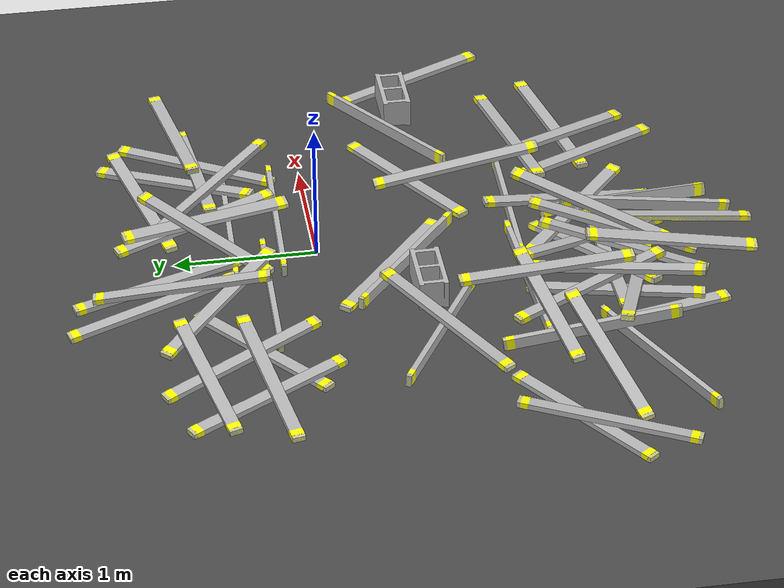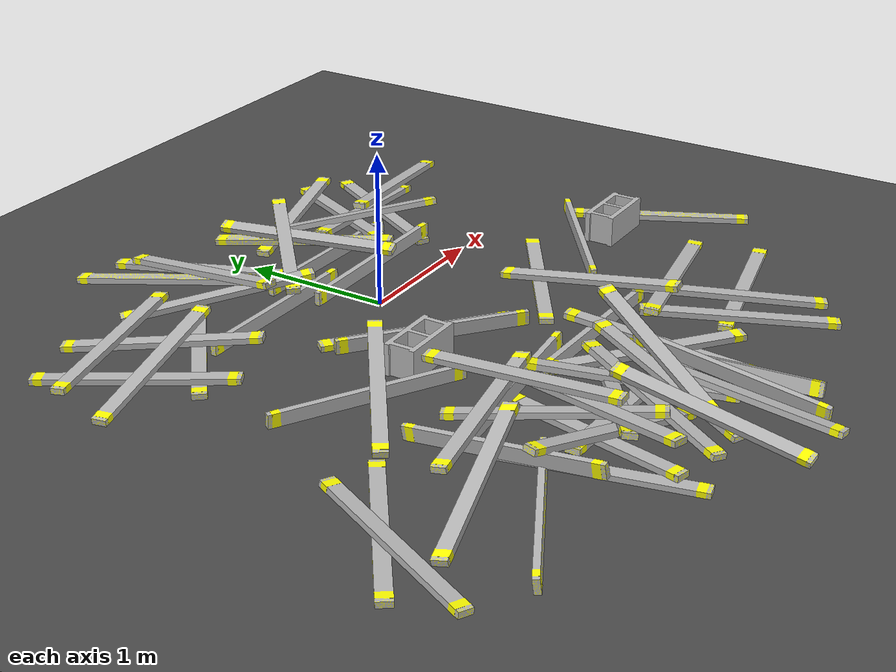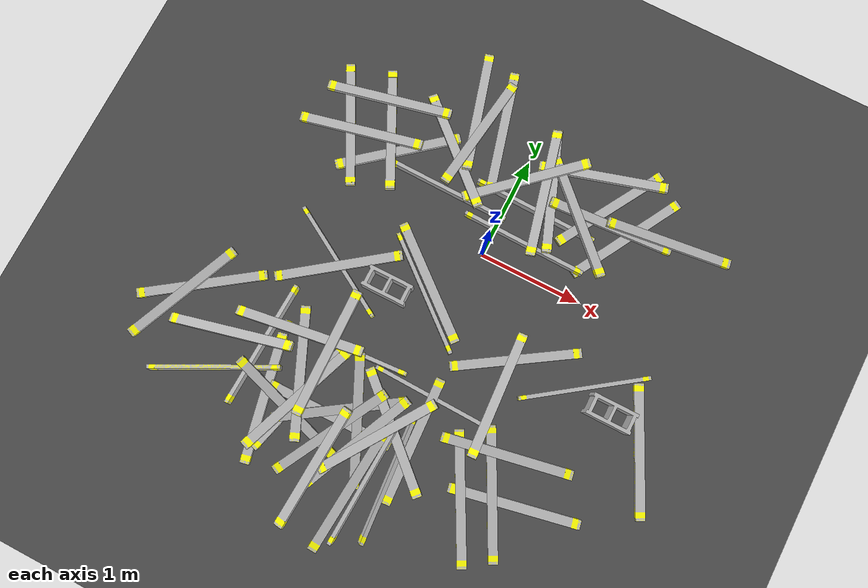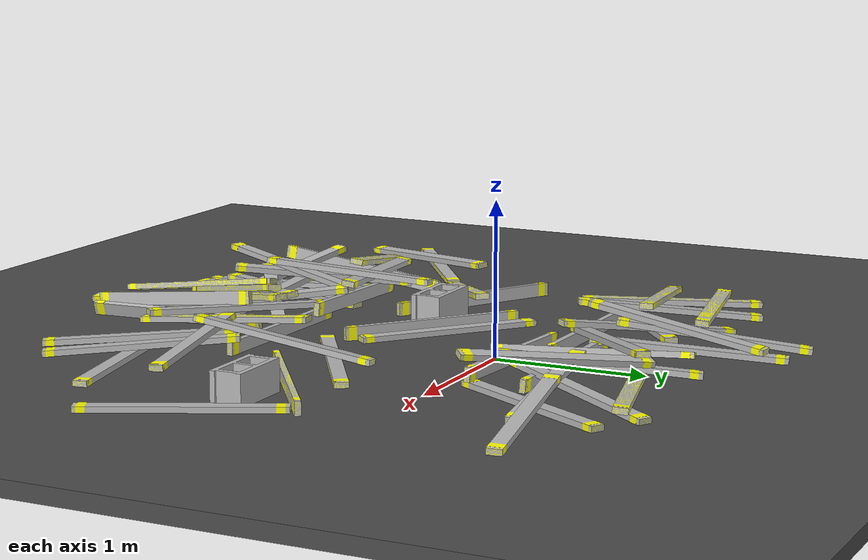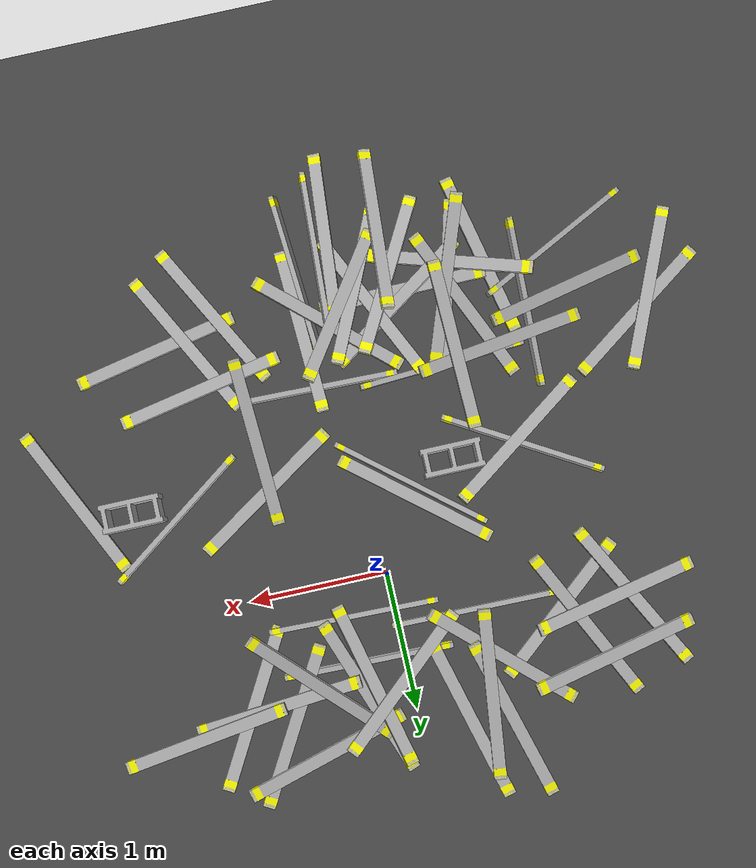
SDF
<sdf version="1.6">
 <world name="default">
  <light name="sun" type="directional">
   <pose>0 0 10 0 -0 0</pose>
   <diffuse>0.8 0.8 0.8 1</diffuse>
   <specular>0.1 0.1 0.1 1</specular>
   <attenuation>
    <range>1000</range>
    <constant>0.9</constant>
    <linear>0.01</linear>
    <quadratic>0.001</quadratic>
   </attenuation>
   <direction>-0.5 0.5 -1</direction>
  </light>
  <model name="ground_plane">
   <static>1</static>
   <link name="link">
    <collision name="collision">
     <geometry><plane><normal>0 0 1</normal><size>100 100</size></plane></geometry>
     <surface><friction><ode><mu>100</mu><mu2>50</mu2></ode></friction></surface>
    </collision>
    <visual name="visual">
     <cast_shadows>0</cast_shadows>
     <geometry><plane><normal>0 0 1</normal><size>100 100</size></plane></geometry>
     <material>
      <script><uri>file://media/materials/scripts/gazebo.material</uri><name>Gazebo/Grey</name></script>
     </material>
    </visual>
   </link>
  </model>
  <gravity>0 0 -9.8</gravity>
  <magnetic_field>6e-06 2.3e-05 -4.2e-05</magnetic_field>
  <atmosphere type="adiabatic"/>
  <physics name="default_physics" default="0" type="ode">
   <max_step_size>0.001</max_step_size>
   <real_time_factor>1</real_time_factor>
   <real_time_update_rate>1000</real_time_update_rate>
  </physics>
  <scene><ambient>0.4 0.4 0.4 1</ambient><background>0.7 0.7 0.7 1</background><shadows>1</shadows></scene>
  <spherical_coordinates>
   <surface_model>EARTH_WGS84</surface_model>
   <latitude_deg>0</latitude_deg>
   <longitude_deg>0</longitude_deg>
   <elevation>0</elevation>
   <heading_deg>0</heading_deg>
  </spherical_coordinates>
  <model name="asphalt_plane">
   <static>1</static>
   <link name="link">
    <collision name="collision"><geometry><box><size>20 20 0.1</size></box></geometry></collision>
    <visual name="visual">
     <cast_shadows>0</cast_shadows>
     <geometry><box><size>20 20 0.1</size></box></geometry>
     <material>
      <script>
       <uri>model://asphalt_plane/materials/scripts</uri>
       <uri>model://asphalt_plane/materials/textures</uri>
       <name>vrc/asphalt</name>
      </script>
     </material>
    </visual>
   </link>
   <pose>0.013797 -0.037077 0 0 -0 0</pose>
  </model>
  <model name="lumber_2x4x48">
   <link name="link">
    <inertial>
     <mass>1.4111</mass>
     <inertia><ixx>0.0011</ixx><ixy>0</ixy><ixz>0</ixz><iyy>0.1771</iyy><iyz>0</iyz><izz>0.1763</izz></inertia>
    </inertial>
    <collision name="collision">
     <geometry><box><size>1.2192 0.038 0.0888</size></box></geometry>
     <surface>
      <bounce><restitution_coefficient>0.01</restitution_coefficient><threshold>5</threshold></bounce>
      <friction><ode><mu>5</mu><mu2>5</mu2></ode></friction>
      <contact>
       <ode>
        <soft_cfm>0.001</soft_cfm>
        <kp>10000</kp>
        <kd>1000</kd>
        <max_vel>0.01</max_vel>
        <min_depth>0.001</min_depth>
       </ode>
      </contact>
     </surface>
    </collision>
    <visual name="visual">
     <geometry><mesh><uri>model://drc_practice_2x4/meshes/2x4x48.dae</uri><scale>1 1 1</scale></mesh></geometry>
    </visual>
   </link>
   <pose>0.295808 0.248092 0.112008 0.001845 -0.031467 -0.025889</pose>
  </model>
  <model name="lumber_2x4x48_clone">
   <link name="link">
    <inertial>
     <mass>1.4111</mass>
     <inertia><ixx>0.0011</ixx><ixy>0</ixy><ixz>0</ixz><iyy>0.1771</iyy><iyz>0</iyz><izz>0.1763</izz></inertia>
    </inertial>
    <collision name="collision">
     <geometry><box><size>1.2192 0.038 0.0888</size></box></geometry>
     <surface>
      <bounce><restitution_coefficient>0.01</restitution_coefficient><threshold>5</threshold></bounce>
      <friction><ode><mu>5</mu><mu2>5</mu2></ode></friction>
      <contact>
       <ode>
        <soft_cfm>0.001</soft_cfm>
        <kp>10000</kp>
        <kd>1000</kd>
        <max_vel>0.01</max_vel>
        <min_depth>0.001</min_depth>
       </ode>
      </contact>
     </surface>
    </collision>
    <visual name="visual">
     <geometry><mesh><uri>model://drc_practice_2x4/meshes/2x4x48.dae</uri><scale>1 1 1</scale></mesh></geometry>
    </visual>
   </link>
   <pose>-0.564844 0.385087 0.092446 -0.014603 -0.000898 -0.013555</pose>
  </model>
  <model name="lumber_2x4x48_clone_1">
   <link name="link">
    <inertial>
     <mass>1.4111</mass>
     <inertia><ixx>0.0011</ixx><ixy>0</ixy><ixz>0</ixz><iyy>0.1771</iyy><iyz>0</iyz><izz>0.1763</izz></inertia>
    </inertial>
    <collision name="collision">
     <geometry><box><size>1.2192 0.038 0.0888</size></box></geometry>
     <surface>
      <bounce><restitution_coefficient>0.01</restitution_coefficient><threshold>5</threshold></bounce>
      <friction><ode><mu>5</mu><mu2>5</mu2></ode></friction>
      <contact>
       <ode>
        <soft_cfm>0.001</soft_cfm>
        <kp>10000</kp>
        <kd>1000</kd>
        <max_vel>0.01</max_vel>
        <min_depth>0.001</min_depth>
       </ode>
      </contact>
     </surface>
    </collision>
    <visual name="visual">
     <geometry><mesh><uri>model://drc_practice_2x4/meshes/2x4x48.dae</uri><scale>1 1 1</scale></mesh></geometry>
    </visual>
   </link>
   <pose>0.260045 0.582681 0.088609 -0.085034 0.000438 -0.022643</pose>
  </model>
  <model name="lumber_2x4x48_clone_3_clone">
   <link name="link">
    <inertial>
     <mass>1.4111</mass>
     <inertia><ixx>0.0011</ixx><ixy>0</ixy><ixz>0</ixz><iyy>0.1771</iyy><iyz>0</iyz><izz>0.1763</izz></inertia>
    </inertial>
    <collision name="collision">
     <geometry><box><size>1.2192 0.038 0.0888</size></box></geometry>
     <surface>
      <bounce><restitution_coefficient>0.01</restitution_coefficient><threshold>5</threshold></bounce>
      <friction><ode><mu>5</mu><mu2>5</mu2></ode></friction>
      <contact>
       <ode>
        <soft_cfm>0.001</soft_cfm>
        <kp>10000</kp>
        <kd>1000</kd>
        <max_vel>0.01</max_vel>
        <min_depth>0.001</min_depth>
       </ode>
      </contact>
     </surface>
    </collision>
    <visual name="visual">
     <geometry><mesh><uri>model://drc_practice_2x4/meshes/2x4x48.dae</uri><scale>1 1 1</scale></mesh></geometry>
    </visual>
   </link>
   <pose>-0.674077 0.751411 0.144054 1.58243 -0.126257 -0.74308</pose>
  </model>
  <model name="lumber_2x4x48_clone_3_clone_0">
   <link name="link">
    <inertial>
     <mass>1.4111</mass>
     <inertia><ixx>0.0011</ixx><ixy>0</ixy><ixz>0</ixz><iyy>0.1771</iyy><iyz>0</iyz><izz>0.1763</izz></inertia>
    </inertial>
    <collision name="collision">
     <geometry><box><size>1.2192 0.038 0.0888</size></box></geometry>
     <surface>
      <bounce><restitution_coefficient>0.01</restitution_coefficient><threshold>5</threshold></bounce>
      <friction><ode><mu>5</mu><mu2>5</mu2></ode></friction>
      <contact>
       <ode>
        <soft_cfm>0.001</soft_cfm>
        <kp>10000</kp>
        <kd>1000</kd>
        <max_vel>0.01</max_vel>
        <min_depth>0.001</min_depth>
       </ode>
      </contact>
     </surface>
    </collision>
    <visual name="visual">
     <geometry><mesh><uri>model://drc_practice_2x4/meshes/2x4x48.dae</uri><scale>1 1 1</scale></mesh></geometry>
    </visual>
   </link>
   <pose>0.052465 0.772468 0.212317 1.53337 -0.090895 0.715596</pose>
  </model>
  <model name="lumber_2x4x48_clone_3_clone_0_clone_1">
   <link name="link">
    <inertial>
     <mass>1.4111</mass>
     <inertia><ixx>0.0011</ixx><ixy>0</ixy><ixz>0</ixz><iyy>0.1771</iyy><iyz>0</iyz><izz>0.1763</izz></inertia>
    </inertial>
    <collision name="collision">
     <geometry><box><size>1.2192 0.038 0.0888</size></box></geometry>
     <surface>
      <bounce><restitution_coefficient>0.01</restitution_coefficient><threshold>5</threshold></bounce>
      <friction><ode><mu>5</mu><mu2>5</mu2></ode></friction>
      <contact>
       <ode>
        <soft_cfm>0.001</soft_cfm>
        <kp>10000</kp>
        <kd>1000</kd>
        <max_vel>0.01</max_vel>
        <min_depth>0.001</min_depth>
       </ode>
      </contact>
     </surface>
    </collision>
    <visual name="visual">
     <geometry><mesh><uri>model://drc_practice_2x4/meshes/2x4x48.dae</uri><scale>1 1 1</scale></mesh></geometry>
    </visual>
   </link>
   <pose>-0.536621 0.990716 0.198915 1.59843 0.135989 1.45668</pose>
  </model>
  <model name="lumber_2x4x48_clone_1_clone">
   <link name="link">
    <inertial>
     <mass>1.4111</mass>
     <inertia><ixx>0.0011</ixx><ixy>0</ixy><ixz>0</ixz><iyy>0.1771</iyy><iyz>0</iyz><izz>0.1763</izz></inertia>
    </inertial>
    <collision name="collision">
     <geometry><box><size>1.2192 0.038 0.0888</size></box></geometry>
     <surface>
      <bounce><restitution_coefficient>0.01</restitution_coefficient><threshold>5</threshold></bounce>
      <friction><ode><mu>5</mu><mu2>5</mu2></ode></friction>
      <contact>
       <ode>
        <soft_cfm>0.001</soft_cfm>
        <kp>10000</kp>
        <kd>1000</kd>
        <max_vel>0.01</max_vel>
        <min_depth>0.001</min_depth>
       </ode>
      </contact>
     </surface>
    </collision>
    <visual name="visual">
     <geometry><mesh><uri>model://drc_practice_2x4/meshes/2x4x48.dae</uri><scale>1 1 1</scale></mesh></geometry>
    </visual>
   </link>
   <pose>-0.551399 -1.96521 0.104119 -1.58274 0.059663 -0.000419</pose>
  </model>
  <model name="lumber_2x4x48_clone_3_clone_0_clone_0_clone">
   <link name="link">
    <inertial>
     <mass>1.4111</mass>
     <inertia><ixx>0.0011</ixx><ixy>0</ixy><ixz>0</ixz><iyy>0.1771</iyy><iyz>0</iyz><izz>0.1763</izz></inertia>
    </inertial>
    <collision name="collision">
     <geometry><box><size>1.2192 0.038 0.0888</size></box></geometry>
     <surface>
      <bounce><restitution_coefficient>0.01</restitution_coefficient><threshold>5</threshold></bounce>
      <friction><ode><mu>5</mu><mu2>5</mu2></ode></friction>
      <contact>
       <ode>
        <soft_cfm>0.001</soft_cfm>
        <kp>10000</kp>
        <kd>1000</kd>
        <max_vel>0.01</max_vel>
        <min_depth>0.001</min_depth>
       </ode>
      </contact>
     </surface>
    </collision>
    <visual name="visual">
     <geometry><mesh><uri>model://drc_practice_2x4/meshes/2x4x48.dae</uri><scale>1 1 1</scale></mesh></geometry>
    </visual>
   </link>
   <pose>-0.491095 -1.8733 0.143896 1.68395 0.124145 0.588669</pose>
  </model>
  <model name="lumber_2x4x48_clone_3_clone_0_clone_0_clone_0">
   <link name="link">
    <inertial>
     <mass>1.4111</mass>
     <inertia><ixx>0.0011</ixx><ixy>0</ixy><ixz>0</ixz><iyy>0.1771</iyy><iyz>0</iyz><izz>0.1763</izz></inertia>
    </inertial>
    <collision name="collision">
     <geometry><box><size>1.2192 0.038 0.0888</size></box></geometry>
     <surface>
      <bounce><restitution_coefficient>0.01</restitution_coefficient><threshold>5</threshold></bounce>
      <friction><ode><mu>5</mu><mu2>5</mu2></ode></friction>
      <contact>
       <ode>
        <soft_cfm>0.001</soft_cfm>
        <kp>10000</kp>
        <kd>1000</kd>
        <max_vel>0.01</max_vel>
        <min_depth>0.001</min_depth>
       </ode>
      </contact>
     </surface>
    </collision>
    <visual name="visual">
     <geometry><mesh><uri>model://drc_practice_2x4/meshes/2x4x48.dae</uri><scale>1 1 1</scale></mesh></geometry>
    </visual>
   </link>
   <pose>0.026145 -1.83286 0.153385 1.53811 0.032401 2.41172</pose>
  </model>
  <model name="lumber_2x4x48_clone_3_clone_0_clone_0_clone_0_clone">
   <link name="link">
    <inertial>
     <mass>1.4111</mass>
     <inertia><ixx>0.0011</ixx><ixy>0</ixy><ixz>0</ixz><iyy>0.1771</iyy><iyz>0</iyz><izz>0.1763</izz></inertia>
    </inertial>
    <collision name="collision">
     <geometry><box><size>1.2192 0.038 0.0888</size></box></geometry>
     <surface>
      <bounce><restitution_coefficient>0.01</restitution_coefficient><threshold>5</threshold></bounce>
      <friction><ode><mu>5</mu><mu2>5</mu2></ode></friction>
      <contact>
       <ode>
        <soft_cfm>0.001</soft_cfm>
        <kp>10000</kp>
        <kd>1000</kd>
        <max_vel>0.01</max_vel>
        <min_depth>0.001</min_depth>
       </ode>
      </contact>
     </surface>
    </collision>
    <visual name="visual">
     <geometry><mesh><uri>model://drc_practice_2x4/meshes/2x4x48.dae</uri><scale>1 1 1</scale></mesh></geometry>
    </visual>
   </link>
   <pose>-0.9154 -2.08029 0.176265 1.59063 -0.182362 2.80756</pose>
  </model>
  <model name="lumber_2x4x48_clone_0_clone">
   <link name="link">
    <inertial>
     <mass>1.4111</mass>
     <inertia><ixx>0.0011</ixx><ixy>0</ixy><ixz>0</ixz><iyy>0.1771</iyy><iyz>0</iyz><izz>0.1763</izz></inertia>
    </inertial>
    <collision name="collision">
     <geometry><box><size>1.2192 0.038 0.0888</size></box></geometry>
     <surface>
      <bounce><restitution_coefficient>0.01</restitution_coefficient><threshold>5</threshold></bounce>
      <friction><ode><mu>5</mu><mu2>5</mu2></ode></friction>
      <contact>
       <ode>
        <soft_cfm>0.001</soft_cfm>
        <kp>10000</kp>
        <kd>1000</kd>
        <max_vel>0.01</max_vel>
        <min_depth>0.001</min_depth>
       </ode>
      </contact>
     </surface>
    </collision>
    <visual name="visual">
     <geometry><mesh><uri>model://drc_practice_2x4/meshes/2x4x48.dae</uri><scale>1 1 1</scale></mesh></geometry>
    </visual>
   </link>
   <pose>-0.710457 -1.3682 0.129535 -0.070083 -0.054685 0.065202</pose>
  </model>
  <model name="lumber_2x4x48_clone_0_clone_0">
   <link name="link">
    <inertial>
     <mass>1.4111</mass>
     <inertia><ixx>0.0011</ixx><ixy>0</ixy><ixz>0</ixz><iyy>0.1771</iyy><iyz>0</iyz><izz>0.1763</izz></inertia>
    </inertial>
    <collision name="collision">
     <geometry><box><size>1.2192 0.038 0.0888</size></box></geometry>
     <surface>
      <bounce><restitution_coefficient>0.01</restitution_coefficient><threshold>5</threshold></bounce>
      <friction><ode><mu>5</mu><mu2>5</mu2></ode></friction>
      <contact>
       <ode>
        <soft_cfm>0.001</soft_cfm>
        <kp>10000</kp>
        <kd>1000</kd>
        <max_vel>0.01</max_vel>
        <min_depth>0.001</min_depth>
       </ode>
      </contact>
     </surface>
    </collision>
    <visual name="visual">
     <geometry><mesh><uri>model://drc_practice_2x4/meshes/2x4x48.dae</uri><scale>1 1 1</scale></mesh></geometry>
    </visual>
   </link>
   <pose>0.224612 -1.4017 0.09229 0.001289 0.001106 -0.02268</pose>
  </model>
  <model name="lumber_2x4x48_clone_3_clone_0_clone_1_clone">
   <link name="link">
    <inertial>
     <mass>1.4111</mass>
     <inertia><ixx>0.0011</ixx><ixy>0</ixy><ixz>0</ixz><iyy>0.1771</iyy><iyz>0</iyz><izz>0.1763</izz></inertia>
    </inertial>
    <collision name="collision">
     <geometry><box><size>1.2192 0.038 0.0888</size></box></geometry>
     <surface>
      <bounce><restitution_coefficient>0.01</restitution_coefficient><threshold>5</threshold></bounce>
      <friction><ode><mu>5</mu><mu2>5</mu2></ode></friction>
      <contact>
       <ode>
        <soft_cfm>0.001</soft_cfm>
        <kp>10000</kp>
        <kd>1000</kd>
        <max_vel>0.01</max_vel>
        <min_depth>0.001</min_depth>
       </ode>
      </contact>
     </surface>
    </collision>
    <visual name="visual">
     <geometry><mesh><uri>model://drc_practice_2x4/meshes/2x4x48.dae</uri><scale>1 1 1</scale></mesh></geometry>
    </visual>
   </link>
   <pose>-0.878822 -1.94492 0.085398 1.56353 0.03198 1.3131</pose>
  </model>
  <model name="lumber_2x4x48_clone_3_clone_0_clone_1_clone_clone">
   <link name="link">
    <inertial>
     <mass>1.4111</mass>
     <inertia><ixx>0.0011</ixx><ixy>0</ixy><ixz>0</ixz><iyy>0.1771</iyy><iyz>0</iyz><izz>0.1763</izz></inertia>
    </inertial>
    <collision name="collision">
     <geometry><box><size>1.2192 0.038 0.0888</size></box></geometry>
     <surface>
      <bounce><restitution_coefficient>0.01</restitution_coefficient><threshold>5</threshold></bounce>
      <friction><ode><mu>5</mu><mu2>5</mu2></ode></friction>
      <contact>
       <ode>
        <soft_cfm>0.001</soft_cfm>
        <kp>10000</kp>
        <kd>1000</kd>
        <max_vel>0.01</max_vel>
        <min_depth>0.001</min_depth>
       </ode>
      </contact>
     </surface>
    </collision>
    <visual name="visual">
     <geometry><mesh><uri>model://drc_practice_2x4/meshes/2x4x48.dae</uri><scale>1 1 1</scale></mesh></geometry>
    </visual>
   </link>
   <pose>0.005661 -2.34814 0.162238 -0.131373 -0.111052 1.52374</pose>
  </model>
  <model name="lumber_2x4x48_clone_3_clone_0_clone_1_clone_clone_1">
   <link name="link">
    <inertial>
     <mass>1.4111</mass>
     <inertia><ixx>0.0011</ixx><ixy>0</ixy><ixz>0</ixz><iyy>0.1771</iyy><iyz>0</iyz><izz>0.1763</izz></inertia>
    </inertial>
    <collision name="collision">
     <geometry><box><size>1.2192 0.038 0.0888</size></box></geometry>
     <surface>
      <bounce><restitution_coefficient>0.01</restitution_coefficient><threshold>5</threshold></bounce>
      <friction><ode><mu>5</mu><mu2>5</mu2></ode></friction>
      <contact>
       <ode>
        <soft_cfm>0.001</soft_cfm>
        <kp>10000</kp>
        <kd>1000</kd>
        <max_vel>0.01</max_vel>
        <min_depth>0.001</min_depth>
       </ode>
      </contact>
     </surface>
    </collision>
    <visual name="visual">
     <geometry><mesh><uri>model://drc_practice_2x4/meshes/2x4x48.dae</uri><scale>1 1 1</scale></mesh></geometry>
    </visual>
   </link>
   <pose>-1.38732 -1.67393 0.170197 3.0514 0.126034 1.55885</pose>
  </model>
  <model name="lumber_2x4x48_clone_3_clone_0_clone_1_clone_clone_2">
   <link name="link">
    <inertial>
     <mass>1.4111</mass>
     <inertia><ixx>0.0011</ixx><ixy>0</ixy><ixz>0</ixz><iyy>0.1771</iyy><iyz>0</iyz><izz>0.1763</izz></inertia>
    </inertial>
    <collision name="collision">
     <geometry><box><size>1.2192 0.038 0.0888</size></box></geometry>
     <surface>
      <bounce><restitution_coefficient>0.01</restitution_coefficient><threshold>5</threshold></bounce>
      <friction><ode><mu>5</mu><mu2>5</mu2></ode></friction>
      <contact>
       <ode>
        <soft_cfm>0.001</soft_cfm>
        <kp>10000</kp>
        <kd>1000</kd>
        <max_vel>0.01</max_vel>
        <min_depth>0.001</min_depth>
       </ode>
      </contact>
     </surface>
    </collision>
    <visual name="visual">
     <geometry><mesh><uri>model://drc_practice_2x4/meshes/2x4x48.dae</uri><scale>1 1 1</scale></mesh></geometry>
    </visual>
   </link>
   <pose>-1.69019 -2.06852 0.107609 -0.127922 -0.022376 0.469954</pose>
  </model>
  <model name="lumber_2x4x48_clone_3_clone_0_clone_clone">
   <link name="link">
    <inertial>
     <mass>1.4111</mass>
     <inertia><ixx>0.0011</ixx><ixy>0</ixy><ixz>0</ixz><iyy>0.1771</iyy><iyz>0</iyz><izz>0.1763</izz></inertia>
    </inertial>
    <collision name="collision">
     <geometry><box><size>1.2192 0.038 0.0888</size></box></geometry>
     <surface>
      <bounce><restitution_coefficient>0.01</restitution_coefficient><threshold>5</threshold></bounce>
      <friction><ode><mu>5</mu><mu2>5</mu2></ode></friction>
      <contact>
       <ode>
        <soft_cfm>0.001</soft_cfm>
        <kp>10000</kp>
        <kd>1000</kd>
        <max_vel>0.01</max_vel>
        <min_depth>0.001</min_depth>
       </ode>
      </contact>
     </surface>
    </collision>
    <visual name="visual">
     <geometry><mesh><uri>model://drc_practice_2x4/meshes/2x4x48.dae</uri><scale>1 1 1</scale></mesh></geometry>
    </visual>
   </link>
   <pose>-2.18032 -1.45176 0.067309 1.57859 -0.000151 0.618251</pose>
  </model>
  <model name="lumber_2x4x48_clone_3_clone_0_clone_clone_0">
   <link name="link">
    <inertial>
     <mass>1.4111</mass>
     <inertia><ixx>0.0011</ixx><ixy>0</ixy><ixz>0</ixz><iyy>0.1771</iyy><iyz>0</iyz><izz>0.1763</izz></inertia>
    </inertial>
    <collision name="collision">
     <geometry><box><size>1.2192 0.038 0.0888</size></box></geometry>
     <surface>
      <bounce><restitution_coefficient>0.01</restitution_coefficient><threshold>5</threshold></bounce>
      <friction><ode><mu>5</mu><mu2>5</mu2></ode></friction>
      <contact>
       <ode>
        <soft_cfm>0.001</soft_cfm>
        <kp>10000</kp>
        <kd>1000</kd>
        <max_vel>0.01</max_vel>
        <min_depth>0.001</min_depth>
       </ode>
      </contact>
     </surface>
    </collision>
    <visual name="visual">
     <geometry><mesh><uri>model://drc_practice_2x4/meshes/2x4x48.dae</uri><scale>1 1 1</scale></mesh></geometry>
    </visual>
   </link>
   <pose>1.38165 -0.697669 0.093055 3.14159 0 0.626237</pose>
  </model>
  <model name="lumber_2x4x48_clone_3_clone_0_clone_1_clone_clone_4">
   <link name="link">
    <inertial>
     <mass>1.4111</mass>
     <inertia><ixx>0.0011</ixx><ixy>0</ixy><ixz>0</ixz><iyy>0.1771</iyy><iyz>0</iyz><izz>0.1763</izz></inertia>
    </inertial>
    <collision name="collision">
     <geometry><box><size>1.2192 0.038 0.0888</size></box></geometry>
     <surface>
      <bounce><restitution_coefficient>0.01</restitution_coefficient><threshold>5</threshold></bounce>
      <friction><ode><mu>5</mu><mu2>5</mu2></ode></friction>
      <contact>
       <ode>
        <soft_cfm>0.001</soft_cfm>
        <kp>10000</kp>
        <kd>1000</kd>
        <max_vel>0.01</max_vel>
        <min_depth>0.001</min_depth>
       </ode>
      </contact>
     </surface>
    </collision>
    <visual name="visual">
     <geometry><mesh><uri>model://drc_practice_2x4/meshes/2x4x48.dae</uri><scale>1 1 1</scale></mesh></geometry>
    </visual>
   </link>
   <pose>-1.15883 0.514226 0.067235 1.56227 -0.000503 0.690635</pose>
  </model>
  <model name="lumber_2x4x48_clone_3_clone_0_clone_1_clone_0">
   <link name="link">
    <inertial>
     <mass>1.4111</mass>
     <inertia><ixx>0.0011</ixx><ixy>0</ixy><ixz>0</ixz><iyy>0.1771</iyy><iyz>0</iyz><izz>0.1763</izz></inertia>
    </inertial>
    <collision name="collision">
     <geometry><box><size>1.2192 0.038 0.0888</size></box></geometry>
     <surface>
      <bounce><restitution_coefficient>0.01</restitution_coefficient><threshold>5</threshold></bounce>
      <friction><ode><mu>5</mu><mu2>5</mu2></ode></friction>
      <contact>
       <ode>
        <soft_cfm>0.001</soft_cfm>
        <kp>10000</kp>
        <kd>1000</kd>
        <max_vel>0.01</max_vel>
        <min_depth>0.001</min_depth>
       </ode>
      </contact>
     </surface>
    </collision>
    <visual name="visual">
     <geometry><mesh><uri>model://drc_practice_2x4/meshes/2x4x48.dae</uri><scale>1 1 1</scale></mesh></geometry>
    </visual>
   </link>
   <pose>0.257048 0.749768 0.18857 1.33624 -0.008162 1.81131</pose>
  </model>
  <model name="lumber_2x4x48_clone_3_clone_0_clone_1_clone_1">
   <link name="link">
    <inertial>
     <mass>1.4111</mass>
     <inertia><ixx>0.0011</ixx><ixy>0</ixy><ixz>0</ixz><iyy>0.1771</iyy><iyz>0</iyz><izz>0.1763</izz></inertia>
    </inertial>
    <collision name="collision">
     <geometry><box><size>1.2192 0.038 0.0888</size></box></geometry>
     <surface>
      <bounce><restitution_coefficient>0.01</restitution_coefficient><threshold>5</threshold></bounce>
      <friction><ode><mu>5</mu><mu2>5</mu2></ode></friction>
      <contact>
       <ode>
        <soft_cfm>0.001</soft_cfm>
        <kp>10000</kp>
        <kd>1000</kd>
        <max_vel>0.01</max_vel>
        <min_depth>0.001</min_depth>
       </ode>
      </contact>
     </surface>
    </collision>
    <visual name="visual">
     <geometry><mesh><uri>model://drc_practice_2x4/meshes/2x4x48.dae</uri><scale>1 1 1</scale></mesh></geometry>
    </visual>
   </link>
   <pose>-0.091835 -2.47497 0.109513 -1.70391 0.05927 -1.65204</pose>
  </model>
  <model name="lumber_2x4x48_clone_3_clone_0_clone_1_clone_2">
   <link name="link">
    <inertial>
     <mass>1.4111</mass>
     <inertia><ixx>0.0011</ixx><ixy>0</ixy><ixz>0</ixz><iyy>0.1771</iyy><iyz>0</iyz><izz>0.1763</izz></inertia>
    </inertial>
    <collision name="collision">
     <geometry><box><size>1.2192 0.038 0.0888</size></box></geometry>
     <surface>
      <bounce><restitution_coefficient>0.01</restitution_coefficient><threshold>5</threshold></bounce>
      <friction><ode><mu>5</mu><mu2>5</mu2></ode></friction>
      <contact>
       <ode>
        <soft_cfm>0.001</soft_cfm>
        <kp>10000</kp>
        <kd>1000</kd>
        <max_vel>0.01</max_vel>
        <min_depth>0.001</min_depth>
       </ode>
      </contact>
     </surface>
    </collision>
    <visual name="visual">
     <geometry><mesh><uri>model://drc_practice_2x4/meshes/2x4x48.dae</uri><scale>1 1 1</scale></mesh></geometry>
    </visual>
   </link>
   <pose>0.22247 -1.8259 0.119162 -1.5659 0.084542 -1.52032</pose>
  </model>
  <model name="lumber_2x4x48_clone_3_clone_0_clone_clone_0_clone_0">
   <link name="link">
    <inertial>
     <mass>1.4111</mass>
     <inertia><ixx>0.0011</ixx><ixy>0</ixy><ixz>0</ixz><iyy>0.1771</iyy><iyz>0</iyz><izz>0.1763</izz></inertia>
    </inertial>
    <collision name="collision">
     <geometry><box><size>1.2192 0.038 0.0888</size></box></geometry>
     <surface>
      <bounce><restitution_coefficient>0.01</restitution_coefficient><threshold>5</threshold></bounce>
      <friction><ode><mu>5</mu><mu2>5</mu2></ode></friction>
      <contact>
       <ode>
        <soft_cfm>0.001</soft_cfm>
        <kp>10000</kp>
        <kd>1000</kd>
        <max_vel>0.01</max_vel>
        <min_depth>0.001</min_depth>
       </ode>
      </contact>
     </surface>
    </collision>
    <visual name="visual">
     <geometry><mesh><uri>model://drc_practice_2x4/meshes/2x4x48.dae</uri><scale>1 1 1</scale></mesh></geometry>
    </visual>
   </link>
   <pose>-0.9562 -1.74736 0.203667 -1.65018 -0.07961 -1.14269</pose>
  </model>
  <model name="lumber_2x4x48_clone_3_clone_0_clone_clone_0_clone_0_clone">
   <link name="link">
    <inertial>
     <mass>1.4111</mass>
     <inertia><ixx>0.0011</ixx><ixy>0</ixy><ixz>0</ixz><iyy>0.1771</iyy><iyz>0</iyz><izz>0.1763</izz></inertia>
    </inertial>
    <collision name="collision">
     <geometry><box><size>1.2192 0.038 0.0888</size></box></geometry>
     <surface>
      <bounce><restitution_coefficient>0.01</restitution_coefficient><threshold>5</threshold></bounce>
      <friction><ode><mu>5</mu><mu2>5</mu2></ode></friction>
      <contact>
       <ode>
        <soft_cfm>0.001</soft_cfm>
        <kp>10000</kp>
        <kd>1000</kd>
        <max_vel>0.01</max_vel>
        <min_depth>0.001</min_depth>
       </ode>
      </contact>
     </surface>
    </collision>
    <visual name="visual">
     <geometry><mesh><uri>model://drc_practice_2x4/meshes/2x4x48.dae</uri><scale>1 1 1</scale></mesh></geometry>
    </visual>
   </link>
   <pose>0.627245 0.678739 0.216849 -1.76817 -0.113845 -0.796282</pose>
  </model>
  <model name="lumber_2x4x48_clone_3_clone_0_clone_clone_0_clone_0_clone_0">
   <link name="link">
    <inertial>
     <mass>1.4111</mass>
     <inertia><ixx>0.0011</ixx><ixy>0</ixy><ixz>0</ixz><iyy>0.1771</iyy><iyz>0</iyz><izz>0.1763</izz></inertia>
    </inertial>
    <collision name="collision">
     <geometry><box><size>1.2192 0.038 0.0888</size></box></geometry>
     <surface>
      <bounce><restitution_coefficient>0.01</restitution_coefficient><threshold>5</threshold></bounce>
      <friction><ode><mu>5</mu><mu2>5</mu2></ode></friction>
      <contact>
       <ode>
        <soft_cfm>0.001</soft_cfm>
        <kp>10000</kp>
        <kd>1000</kd>
        <max_vel>0.01</max_vel>
        <min_depth>0.001</min_depth>
       </ode>
      </contact>
     </surface>
    </collision>
    <visual name="visual">
     <geometry><mesh><uri>model://drc_practice_2x4/meshes/2x4x48.dae</uri><scale>1 1 1</scale></mesh></geometry>
    </visual>
   </link>
   <pose>-0.814449 -1.47296 0.278991 -1.5112 -0.044955 -1.54025</pose>
  </model>
  <model name="lumber_2x4x48_clone_3_clone_0_clone_clone_0_clone_0_clone_2">
   <link name="link">
    <inertial>
     <mass>1.4111</mass>
     <inertia><ixx>0.0011</ixx><ixy>0</ixy><ixz>0</ixz><iyy>0.1771</iyy><iyz>0</iyz><izz>0.1763</izz></inertia>
    </inertial>
    <collision name="collision">
     <geometry><box><size>1.2192 0.038 0.0888</size></box></geometry>
     <surface>
      <bounce><restitution_coefficient>0.01</restitution_coefficient><threshold>5</threshold></bounce>
      <friction><ode><mu>5</mu><mu2>5</mu2></ode></friction>
      <contact>
       <ode>
        <soft_cfm>0.001</soft_cfm>
        <kp>10000</kp>
        <kd>1000</kd>
        <max_vel>0.01</max_vel>
        <min_depth>0.001</min_depth>
       </ode>
      </contact>
     </surface>
    </collision>
    <visual name="visual">
     <geometry><mesh><uri>model://drc_practice_2x4/meshes/2x4x48.dae</uri><scale>1 1 1</scale></mesh></geometry>
    </visual>
   </link>
   <pose>-1.16407 -2.10287 0.065749 -1.54798 -0.000855 -1.35803</pose>
  </model>
  <model name="lumber_2x4x48_clone_3_clone_0_clone_clone_0_clone_0_clone_3">
   <link name="link">
    <inertial>
     <mass>1.4111</mass>
     <inertia><ixx>0.0011</ixx><ixy>0</ixy><ixz>0</ixz><iyy>0.1771</iyy><iyz>0</iyz><izz>0.1763</izz></inertia>
    </inertial>
    <collision name="collision">
     <geometry><box><size>1.2192 0.038 0.0888</size></box></geometry>
     <surface>
      <bounce><restitution_coefficient>0.01</restitution_coefficient><threshold>5</threshold></bounce>
      <friction><ode><mu>5</mu><mu2>5</mu2></ode></friction>
      <contact>
       <ode>
        <soft_cfm>0.001</soft_cfm>
        <kp>10000</kp>
        <kd>1000</kd>
        <max_vel>0.01</max_vel>
        <min_depth>0.001</min_depth>
       </ode>
      </contact>
     </surface>
    </collision>
    <visual name="visual">
     <geometry><mesh><uri>model://drc_practice_2x4/meshes/2x4x48.dae</uri><scale>1 1 1</scale></mesh></geometry>
    </visual>
   </link>
   <pose>-0.357372 1.13559 0.106775 -1.58406 -0.063668 -1.31004</pose>
  </model>
  <model name="lumber_2x4x48_clone_3_clone_0_clone_clone_0_clone_0_clone_4">
   <link name="link">
    <inertial>
     <mass>1.4111</mass>
     <inertia><ixx>0.0011</ixx><ixy>0</ixy><ixz>0</ixz><iyy>0.1771</iyy><iyz>0</iyz><izz>0.1763</izz></inertia>
    </inertial>
    <collision name="collision">
     <geometry><box><size>1.2192 0.038 0.0888</size></box></geometry>
     <surface>
      <bounce><restitution_coefficient>0.01</restitution_coefficient><threshold>5</threshold></bounce>
      <friction><ode><mu>5</mu><mu2>5</mu2></ode></friction>
      <contact>
       <ode>
        <soft_cfm>0.001</soft_cfm>
        <kp>10000</kp>
        <kd>1000</kd>
        <max_vel>0.01</max_vel>
        <min_depth>0.001</min_depth>
       </ode>
      </contact>
     </surface>
    </collision>
    <visual name="visual">
     <geometry><mesh><uri>model://drc_practice_2x4/meshes/2x4x48.dae</uri><scale>1 1 1</scale></mesh></geometry>
    </visual>
   </link>
   <pose>1.05451 -1.91415 0.112177 -1.57149 0.073383 -1.08552</pose>
  </model>
  <model name="lumber_2x4x48_clone_3_clone_0_clone_clone_0_clone_0_clone_5">
   <link name="link">
    <inertial>
     <mass>1.4111</mass>
     <inertia><ixx>0.0011</ixx><ixy>0</ixy><ixz>0</ixz><iyy>0.1771</iyy><iyz>0</iyz><izz>0.1763</izz></inertia>
    </inertial>
    <collision name="collision">
     <geometry><box><size>1.2192 0.038 0.0888</size></box></geometry>
     <surface>
      <bounce><restitution_coefficient>0.01</restitution_coefficient><threshold>5</threshold></bounce>
      <friction><ode><mu>5</mu><mu2>5</mu2></ode></friction>
      <contact>
       <ode>
        <soft_cfm>0.001</soft_cfm>
        <kp>10000</kp>
        <kd>1000</kd>
        <max_vel>0.01</max_vel>
        <min_depth>0.001</min_depth>
       </ode>
      </contact>
     </surface>
    </collision>
    <visual name="visual">
     <geometry><mesh><uri>model://drc_practice_2x4/meshes/2x4x48.dae</uri><scale>1 1 1</scale></mesh></geometry>
    </visual>
   </link>
   <pose>2.07159 -0.974587 0.067749 -1.57444 8.2e-05 -1.12244</pose>
  </model>
  <model name="lumber_2x4x48_clone_3_clone_0_clone_clone_0_clone_0_clone_6">
   <link name="link">
    <inertial>
     <mass>1.4111</mass>
     <inertia><ixx>0.0011</ixx><ixy>0</ixy><ixz>0</ixz><iyy>0.1771</iyy><iyz>0</iyz><izz>0.1763</izz></inertia>
    </inertial>
    <collision name="collision">
     <geometry><box><size>1.2192 0.038 0.0888</size></box></geometry>
     <surface>
      <bounce><restitution_coefficient>0.01</restitution_coefficient><threshold>5</threshold></bounce>
      <friction><ode><mu>5</mu><mu2>5</mu2></ode></friction>
      <contact>
       <ode>
        <soft_cfm>0.001</soft_cfm>
        <kp>10000</kp>
        <kd>1000</kd>
        <max_vel>0.01</max_vel>
        <min_depth>0.001</min_depth>
       </ode>
      </contact>
     </surface>
    </collision>
    <visual name="visual">
     <geometry><mesh><uri>model://drc_practice_2x4/meshes/2x4x48.dae</uri><scale>1 1 1</scale></mesh></geometry>
    </visual>
   </link>
   <pose>-1.68194 0.538962 0.0903 -1.56155 -0.037253 -1.08006</pose>
  </model>
  <model name="lumber_2x4x48_clone_3_clone_0_clone_clone_0_clone_0_clone_7">
   <link name="link">
    <inertial>
     <mass>1.4111</mass>
     <inertia><ixx>0.0011</ixx><ixy>0</ixy><ixz>0</ixz><iyy>0.1771</iyy><iyz>0</iyz><izz>0.1763</izz></inertia>
    </inertial>
    <collision name="collision">
     <geometry><box><size>1.2192 0.038 0.0888</size></box></geometry>
     <surface>
      <bounce><restitution_coefficient>0.01</restitution_coefficient><threshold>5</threshold></bounce>
      <friction><ode><mu>5</mu><mu2>5</mu2></ode></friction>
      <contact>
       <ode>
        <soft_cfm>0.001</soft_cfm>
        <kp>10000</kp>
        <kd>1000</kd>
        <max_vel>0.01</max_vel>
        <min_depth>0.001</min_depth>
       </ode>
      </contact>
     </surface>
    </collision>
    <visual name="visual">
     <geometry><mesh><uri>model://drc_practice_2x4/meshes/2x4x48.dae</uri><scale>1 1 1</scale></mesh></geometry>
    </visual>
   </link>
   <pose>-1.3056 0.664728 0.124248 -1.55753 -0.093838 -1.10502</pose>
  </model>
  <model name="lumber_2x4x48_clone_3_clone_0_clone_clone_0_clone_0_clone_8">
   <link name="link">
    <inertial>
     <mass>1.4111</mass>
     <inertia><ixx>0.0011</ixx><ixy>0</ixy><ixz>0</ixz><iyy>0.1771</iyy><iyz>0</iyz><izz>0.1763</izz></inertia>
    </inertial>
    <collision name="collision">
     <geometry><box><size>1.2192 0.038 0.0888</size></box></geometry>
     <surface>
      <bounce><restitution_coefficient>0.01</restitution_coefficient><threshold>5</threshold></bounce>
      <friction><ode><mu>5</mu><mu2>5</mu2></ode></friction>
      <contact>
       <ode>
        <soft_cfm>0.001</soft_cfm>
        <kp>10000</kp>
        <kd>1000</kd>
        <max_vel>0.01</max_vel>
        <min_depth>0.001</min_depth>
       </ode>
      </contact>
     </surface>
    </collision>
    <visual name="visual">
     <geometry><mesh><uri>model://drc_practice_2x4/meshes/2x4x48.dae</uri><scale>1 1 1</scale></mesh></geometry>
    </visual>
   </link>
   <pose>0.824923 -2.07777 0.101162 1.58706 0.05332 -1.08031</pose>
  </model>
  <model name="lumber_2x4x48_clone_3_clone_0_clone_clone_0_clone_0_clone_0_clone">
   <link name="link">
    <inertial>
     <mass>1.4111</mass>
     <inertia><ixx>0.0011</ixx><ixy>0</ixy><ixz>0</ixz><iyy>0.1771</iyy><iyz>0</iyz><izz>0.1763</izz></inertia>
    </inertial>
    <collision name="collision">
     <geometry><box><size>1.2192 0.038 0.0888</size></box></geometry>
     <surface>
      <bounce><restitution_coefficient>0.01</restitution_coefficient><threshold>5</threshold></bounce>
      <friction><ode><mu>5</mu><mu2>5</mu2></ode></friction>
      <contact>
       <ode>
        <soft_cfm>0.001</soft_cfm>
        <kp>10000</kp>
        <kd>1000</kd>
        <max_vel>0.01</max_vel>
        <min_depth>0.001</min_depth>
       </ode>
      </contact>
     </surface>
    </collision>
    <visual name="visual">
     <geometry><mesh><uri>model://drc_practice_2x4/meshes/2x4x48.dae</uri><scale>1 1 1</scale></mesh></geometry>
    </visual>
   </link>
   <pose>-1.15275 -0.691676 0.093036 0.045143 -0.000124 -0.530444</pose>
  </model>
  <model name="lumber_2x4x48_clone_3_clone_0_clone_clone_0_clone_0_clone_0_clone_0">
   <link name="link">
    <inertial>
     <mass>1.4111</mass>
     <inertia><ixx>0.0011</ixx><ixy>0</ixy><ixz>0</ixz><iyy>0.1771</iyy><iyz>0</iyz><izz>0.1763</izz></inertia>
    </inertial>
    <collision name="collision">
     <geometry><box><size>1.2192 0.038 0.0888</size></box></geometry>
     <surface>
      <bounce><restitution_coefficient>0.01</restitution_coefficient><threshold>5</threshold></bounce>
      <friction><ode><mu>5</mu><mu2>5</mu2></ode></friction>
      <contact>
       <ode>
        <soft_cfm>0.001</soft_cfm>
        <kp>10000</kp>
        <kd>1000</kd>
        <max_vel>0.01</max_vel>
        <min_depth>0.001</min_depth>
       </ode>
      </contact>
     </surface>
    </collision>
    <visual name="visual">
     <geometry><mesh><uri>model://drc_practice_2x4/meshes/2x4x48.dae</uri><scale>1 1 1</scale></mesh></geometry>
    </visual>
   </link>
   <pose>-0.310197 -1.89296 0.141695 -1.65213 0.117011 -1.13992</pose>
  </model>
  <model name="lumber_2x4x48_clone_3_clone_0_clone_clone_0_clone_0_clone_9">
   <link name="link">
    <inertial>
     <mass>1.4111</mass>
     <inertia><ixx>0.0011</ixx><ixy>0</ixy><ixz>0</ixz><iyy>0.1771</iyy><iyz>0</iyz><izz>0.1763</izz></inertia>
    </inertial>
    <collision name="collision">
     <geometry><box><size>1.2192 0.038 0.0888</size></box></geometry>
     <surface>
      <bounce><restitution_coefficient>0.01</restitution_coefficient><threshold>5</threshold></bounce>
      <friction><ode><mu>5</mu><mu2>5</mu2></ode></friction>
      <contact>
       <ode>
        <soft_cfm>0.001</soft_cfm>
        <kp>10000</kp>
        <kd>1000</kd>
        <max_vel>0.01</max_vel>
        <min_depth>0.001</min_depth>
       </ode>
      </contact>
     </surface>
    </collision>
    <visual name="visual">
     <geometry><mesh><uri>model://drc_practice_2x4/meshes/2x4x48.dae</uri><scale>1 1 1</scale></mesh></geometry>
    </visual>
   </link>
   <pose>-0.650271 1.19758 0.13768 -1.58002 -0.11587 -1.29308</pose>
  </model>
  <model name="lumber_2x4x48_clone_3_clone_0_clone_clone_0_clone_0_clone_10">
   <link name="link">
    <inertial>
     <mass>1.4111</mass>
     <inertia><ixx>0.0011</ixx><ixy>0</ixy><ixz>0</ixz><iyy>0.1771</iyy><iyz>0</iyz><izz>0.1763</izz></inertia>
    </inertial>
    <collision name="collision">
     <geometry><box><size>1.2192 0.038 0.0888</size></box></geometry>
     <surface>
      <bounce><restitution_coefficient>0.01</restitution_coefficient><threshold>5</threshold></bounce>
      <friction><ode><mu>5</mu><mu2>5</mu2></ode></friction>
      <contact>
       <ode>
        <soft_cfm>0.001</soft_cfm>
        <kp>10000</kp>
        <kd>1000</kd>
        <max_vel>0.01</max_vel>
        <min_depth>0.001</min_depth>
       </ode>
      </contact>
     </surface>
    </collision>
    <visual name="visual">
     <geometry><mesh><uri>model://drc_practice_2x4/meshes/2x4x48.dae</uri><scale>1 1 1</scale></mesh></geometry>
    </visual>
   </link>
   <pose>0.313771 0.821958 0.130659 -1.53175 -0.086722 -1.22289</pose>
  </model>
  <model name="lumber_2x4x48_clone_3_clone_0_clone_clone_0_clone_0_clone_11">
   <link name="link">
    <inertial>
     <mass>1.4111</mass>
     <inertia><ixx>0.0011</ixx><ixy>0</ixy><ixz>0</ixz><iyy>0.1771</iyy><iyz>0</iyz><izz>0.1763</izz></inertia>
    </inertial>
    <collision name="collision">
     <geometry><box><size>1.2192 0.038 0.0888</size></box></geometry>
     <surface>
      <bounce><restitution_coefficient>0.01</restitution_coefficient><threshold>5</threshold></bounce>
      <friction><ode><mu>5</mu><mu2>5</mu2></ode></friction>
      <contact>
       <ode>
        <soft_cfm>0.001</soft_cfm>
        <kp>10000</kp>
        <kd>1000</kd>
        <max_vel>0.01</max_vel>
        <min_depth>0.001</min_depth>
       </ode>
      </contact>
     </surface>
    </collision>
    <visual name="visual">
     <geometry><mesh><uri>model://drc_practice_2x4/meshes/2x4x48.dae</uri><scale>1 1 1</scale></mesh></geometry>
    </visual>
   </link>
   <pose>-0.223628 -2.06554 0.161285 1.5508 0.153874 -1.99309</pose>
  </model>
  <model name="lumber_2x4x48_clone_3_clone_0_clone_clone_0_clone_0_clone_11_clone">
   <link name="link">
    <inertial>
     <mass>1.4111</mass>
     <inertia><ixx>0.0011</ixx><ixy>0</ixy><ixz>0</ixz><iyy>0.1771</iyy><iyz>0</iyz><izz>0.1763</izz></inertia>
    </inertial>
    <collision name="collision">
     <geometry><box><size>1.2192 0.038 0.0888</size></box></geometry>
     <surface>
      <bounce><restitution_coefficient>0.01</restitution_coefficient><threshold>5</threshold></bounce>
      <friction><ode><mu>5</mu><mu2>5</mu2></ode></friction>
      <contact>
       <ode>
        <soft_cfm>0.001</soft_cfm>
        <kp>10000</kp>
        <kd>1000</kd>
        <max_vel>0.01</max_vel>
        <min_depth>0.001</min_depth>
       </ode>
      </contact>
     </surface>
    </collision>
    <visual name="visual">
     <geometry><mesh><uri>model://drc_practice_2x4/meshes/2x4x48.dae</uri><scale>1 1 1</scale></mesh></geometry>
    </visual>
   </link>
   <pose>-0.08174 -1.9315 0.251746 1.68351 0.190437 -2.15915</pose>
  </model>
  <model name="lumber_2x4x48_clone_3_clone_0_clone_clone_0_clone_0_clone_11_clone_0">
   <link name="link">
    <inertial>
     <mass>1.4111</mass>
     <inertia><ixx>0.0011</ixx><ixy>0</ixy><ixz>0</ixz><iyy>0.1771</iyy><iyz>0</iyz><izz>0.1763</izz></inertia>
    </inertial>
    <collision name="collision">
     <geometry><box><size>1.2192 0.038 0.0888</size></box></geometry>
     <surface>
      <bounce><restitution_coefficient>0.01</restitution_coefficient><threshold>5</threshold></bounce>
      <friction><ode><mu>5</mu><mu2>5</mu2></ode></friction>
      <contact>
       <ode>
        <soft_cfm>0.001</soft_cfm>
        <kp>10000</kp>
        <kd>1000</kd>
        <max_vel>0.01</max_vel>
        <min_depth>0.001</min_depth>
       </ode>
      </contact>
     </surface>
    </collision>
    <visual name="visual">
     <geometry><mesh><uri>model://drc_practice_2x4/meshes/2x4x48.dae</uri><scale>1 1 1</scale></mesh></geometry>
    </visual>
   </link>
   <pose>-0.864387 -1.9492 0.257824 1.57847 -0.102712 -1.91162</pose>
  </model>
  <model name="lumber_2x4x48_clone_3_clone_0_clone_clone_0_clone_0_clone_11_clone_3">
   <link name="link">
    <inertial>
     <mass>1.4111</mass>
     <inertia><ixx>0.0011</ixx><ixy>0</ixy><ixz>0</ixz><iyy>0.1771</iyy><iyz>0</iyz><izz>0.1763</izz></inertia>
    </inertial>
    <collision name="collision">
     <geometry><box><size>1.2192 0.038 0.0888</size></box></geometry>
     <surface>
      <bounce><restitution_coefficient>0.01</restitution_coefficient><threshold>5</threshold></bounce>
      <friction><ode><mu>5</mu><mu2>5</mu2></ode></friction>
      <contact>
       <ode>
        <soft_cfm>0.001</soft_cfm>
        <kp>10000</kp>
        <kd>1000</kd>
        <max_vel>0.01</max_vel>
        <min_depth>0.001</min_depth>
       </ode>
      </contact>
     </surface>
    </collision>
    <visual name="visual">
     <geometry><mesh><uri>model://drc_practice_2x4/meshes/2x4x48.dae</uri><scale>1 1 1</scale></mesh></geometry>
    </visual>
   </link>
   <pose>-0.459548 -2.4328 0.162297 -1.33539 0.139766 -1.64123</pose>
  </model>
  <model name="lumber_2x4x48_clone_3_clone_0_clone_clone_0_clone_0_clone_11_clone_4">
   <link name="link">
    <inertial>
     <mass>1.4111</mass>
     <inertia><ixx>0.0011</ixx><ixy>0</ixy><ixz>0</ixz><iyy>0.1771</iyy><iyz>0</iyz><izz>0.1763</izz></inertia>
    </inertial>
    <collision name="collision">
     <geometry><box><size>1.2192 0.038 0.0888</size></box></geometry>
     <surface>
      <bounce><restitution_coefficient>0.01</restitution_coefficient><threshold>5</threshold></bounce>
      <friction><ode><mu>5</mu><mu2>5</mu2></ode></friction>
      <contact>
       <ode>
        <soft_cfm>0.001</soft_cfm>
        <kp>10000</kp>
        <kd>1000</kd>
        <max_vel>0.01</max_vel>
        <min_depth>0.001</min_depth>
       </ode>
      </contact>
     </surface>
    </collision>
    <visual name="visual">
     <geometry><mesh><uri>model://drc_practice_2x4/meshes/2x4x48.dae</uri><scale>1 1 1</scale></mesh></geometry>
    </visual>
   </link>
   <pose>-0.472753 -2.08597 0.163673 -1.69109 0.099317 -2.06924</pose>
  </model>
  <model name="lumber_2x4x48_clone_3_clone_0_clone_clone_0_clone_0_clone_11_clone_11">
   <link name="link">
    <inertial>
     <mass>1.4111</mass>
     <inertia><ixx>0.0011</ixx><ixy>0</ixy><ixz>0</ixz><iyy>0.1771</iyy><iyz>0</iyz><izz>0.1763</izz></inertia>
    </inertial>
    <collision name="collision">
     <geometry><box><size>1.2192 0.038 0.0888</size></box></geometry>
     <surface>
      <bounce><restitution_coefficient>0.01</restitution_coefficient><threshold>5</threshold></bounce>
      <friction><ode><mu>5</mu><mu2>5</mu2></ode></friction>
      <contact>
       <ode>
        <soft_cfm>0.001</soft_cfm>
        <kp>10000</kp>
        <kd>1000</kd>
        <max_vel>0.01</max_vel>
        <min_depth>0.001</min_depth>
       </ode>
      </contact>
     </surface>
    </collision>
    <visual name="visual">
     <geometry><mesh><uri>model://drc_practice_2x4/meshes/2x4x48.dae</uri><scale>1 1 1</scale></mesh></geometry>
    </visual>
   </link>
   <pose>0.871339 0.913581 0.11193 1.57992 -0.075437 -2.09459</pose>
  </model>
  <model name="lumber_2x4x48_clone_3_clone_0_clone_clone_0_clone_0_clone_11_clone_12">
   <link name="link">
    <inertial>
     <mass>1.4111</mass>
     <inertia><ixx>0.0011</ixx><ixy>0</ixy><ixz>0</ixz><iyy>0.1771</iyy><iyz>0</iyz><izz>0.1763</izz></inertia>
    </inertial>
    <collision name="collision">
     <geometry><box><size>1.2192 0.038 0.0888</size></box></geometry>
     <surface>
      <bounce><restitution_coefficient>0.01</restitution_coefficient><threshold>5</threshold></bounce>
      <friction><ode><mu>5</mu><mu2>5</mu2></ode></friction>
      <contact>
       <ode>
        <soft_cfm>0.001</soft_cfm>
        <kp>10000</kp>
        <kd>1000</kd>
        <max_vel>0.01</max_vel>
        <min_depth>0.001</min_depth>
       </ode>
      </contact>
     </surface>
    </collision>
    <visual name="visual">
     <geometry><mesh><uri>model://drc_practice_2x4/meshes/2x4x48.dae</uri><scale>1 1 1</scale></mesh></geometry>
    </visual>
   </link>
   <pose>1.13104 0.733816 0.067238 1.57761 0.000641 -2.08471</pose>
  </model>
  <model name="lumber_2x4x48_clone_3_clone_0_clone_clone_0_clone_0_clone_11_clone_13">
   <link name="link">
    <inertial>
     <mass>1.4111</mass>
     <inertia><ixx>0.0011</ixx><ixy>0</ixy><ixz>0</ixz><iyy>0.1771</iyy><iyz>0</iyz><izz>0.1763</izz></inertia>
    </inertial>
    <collision name="collision">
     <geometry><box><size>1.2192 0.038 0.0888</size></box></geometry>
     <surface>
      <bounce><restitution_coefficient>0.01</restitution_coefficient><threshold>5</threshold></bounce>
      <friction><ode><mu>5</mu><mu2>5</mu2></ode></friction>
      <contact>
       <ode>
        <soft_cfm>0.001</soft_cfm>
        <kp>10000</kp>
        <kd>1000</kd>
        <max_vel>0.01</max_vel>
        <min_depth>0.001</min_depth>
       </ode>
      </contact>
     </surface>
    </collision>
    <visual name="visual">
     <geometry><mesh><uri>model://drc_practice_2x4/meshes/2x4x48.dae</uri><scale>1 1 1</scale></mesh></geometry>
    </visual>
   </link>
   <pose>0.717379 -0.748609 0.067471 1.57525 -2.1e-05 -2.56666</pose>
  </model>
  <model name="lumber_2x4x48_clone_3_clone_0_clone_clone_0_clone_0_clone_11_clone_14_clone_clone">
   <link name="link">
    <inertial>
     <mass>1.4111</mass>
     <inertia><ixx>0.0011</ixx><ixy>0</ixy><ixz>0</ixz><iyy>0.1771</iyy><iyz>0</iyz><izz>0.1763</izz></inertia>
    </inertial>
    <collision name="collision">
     <geometry><box><size>1.2192 0.038 0.0888</size></box></geometry>
     <surface>
      <bounce><restitution_coefficient>0.01</restitution_coefficient><threshold>5</threshold></bounce>
      <friction><ode><mu>5</mu><mu2>5</mu2></ode></friction>
      <contact>
       <ode>
        <soft_cfm>0.001</soft_cfm>
        <kp>10000</kp>
        <kd>1000</kd>
        <max_vel>0.01</max_vel>
        <min_depth>0.001</min_depth>
       </ode>
      </contact>
     </surface>
    </collision>
    <visual name="visual">
     <geometry><mesh><uri>model://drc_practice_2x4/meshes/2x4x48.dae</uri><scale>1 1 1</scale></mesh></geometry>
    </visual>
   </link>
   <pose>1.28109 -1.92031 0.067274 1.56167 0.000486 -2.93986</pose>
  </model>
  <model name="lumber_2x4x48_clone_3_clone_0_clone_clone_0_clone_0_clone_11_clone_14_clone_clone_0">
   <link name="link">
    <inertial>
     <mass>1.4111</mass>
     <inertia><ixx>0.0011</ixx><ixy>0</ixy><ixz>0</ixz><iyy>0.1771</iyy><iyz>0</iyz><izz>0.1763</izz></inertia>
    </inertial>
    <collision name="collision">
     <geometry><box><size>1.2192 0.038 0.0888</size></box></geometry>
     <surface>
      <bounce><restitution_coefficient>0.01</restitution_coefficient><threshold>5</threshold></bounce>
      <friction><ode><mu>5</mu><mu2>5</mu2></ode></friction>
      <contact>
       <ode>
        <soft_cfm>0.001</soft_cfm>
        <kp>10000</kp>
        <kd>1000</kd>
        <max_vel>0.01</max_vel>
        <min_depth>0.001</min_depth>
       </ode>
      </contact>
     </surface>
    </collision>
    <visual name="visual">
     <geometry><mesh><uri>model://drc_practice_2x4/meshes/2x4x48.dae</uri><scale>1 1 1</scale></mesh></geometry>
    </visual>
   </link>
   <pose>0.685393 1.16674 0.101494 1.65282 0.054821 -2.87109</pose>
  </model>
  <model name="lumber_2x4x48_clone_3_clone_0_clone_clone_0_clone_0_clone_11_clone_14_clone_clone_1">
   <link name="link">
    <inertial>
     <mass>1.4111</mass>
     <inertia><ixx>0.0011</ixx><ixy>0</ixy><ixz>0</ixz><iyy>0.1771</iyy><iyz>0</iyz><izz>0.1763</izz></inertia>
    </inertial>
    <collision name="collision">
     <geometry><box><size>1.2192 0.038 0.0888</size></box></geometry>
     <surface>
      <bounce><restitution_coefficient>0.01</restitution_coefficient><threshold>5</threshold></bounce>
      <friction><ode><mu>5</mu><mu2>5</mu2></ode></friction>
      <contact>
       <ode>
        <soft_cfm>0.001</soft_cfm>
        <kp>10000</kp>
        <kd>1000</kd>
        <max_vel>0.01</max_vel>
        <min_depth>0.001</min_depth>
       </ode>
      </contact>
     </surface>
    </collision>
    <visual name="visual">
     <geometry><mesh><uri>model://drc_practice_2x4/meshes/2x4x48.dae</uri><scale>1 1 1</scale></mesh></geometry>
    </visual>
   </link>
   <pose>0.948398 0.757759 0.138412 1.60284 -0.086825 -3.04838</pose>
  </model>
  <model name="lumber_2x4x48_clone_3_clone_0_clone_clone_0_clone_0_clone_11_clone_14_clone_clone_3">
   <link name="link">
    <inertial>
     <mass>1.4111</mass>
     <inertia><ixx>0.0011</ixx><ixy>0</ixy><ixz>0</ixz><iyy>0.1771</iyy><iyz>0</iyz><izz>0.1763</izz></inertia>
    </inertial>
    <collision name="collision">
     <geometry><box><size>1.2192 0.038 0.0888</size></box></geometry>
     <surface>
      <bounce><restitution_coefficient>0.01</restitution_coefficient><threshold>5</threshold></bounce>
      <friction><ode><mu>5</mu><mu2>5</mu2></ode></friction>
      <contact>
       <ode>
        <soft_cfm>0.001</soft_cfm>
        <kp>10000</kp>
        <kd>1000</kd>
        <max_vel>0.01</max_vel>
        <min_depth>0.001</min_depth>
       </ode>
      </contact>
     </surface>
    </collision>
    <visual name="visual">
     <geometry><mesh><uri>model://drc_practice_2x4/meshes/2x4x48.dae</uri><scale>1 1 1</scale></mesh></geometry>
    </visual>
   </link>
   <pose>-1.55085 0.512558 0.143799 1.57649 0.108251 -2.94985</pose>
  </model>
  <model name="lumber_2x4x48_clone_3_clone_0_clone_clone_0_clone_0_clone_11_clone_14_clone_clone_4">
   <link name="link">
    <inertial>
     <mass>1.4111</mass>
     <inertia><ixx>0.0011</ixx><ixy>0</ixy><ixz>0</ixz><iyy>0.1771</iyy><iyz>0</iyz><izz>0.1763</izz></inertia>
    </inertial>
    <collision name="collision">
     <geometry><box><size>1.2192 0.038 0.0888</size></box></geometry>
     <surface>
      <bounce><restitution_coefficient>0.01</restitution_coefficient><threshold>5</threshold></bounce>
      <friction><ode><mu>5</mu><mu2>5</mu2></ode></friction>
      <contact>
       <ode>
        <soft_cfm>0.001</soft_cfm>
        <kp>10000</kp>
        <kd>1000</kd>
        <max_vel>0.01</max_vel>
        <min_depth>0.001</min_depth>
       </ode>
      </contact>
     </surface>
    </collision>
    <visual name="visual">
     <geometry><mesh><uri>model://drc_practice_2x4/meshes/2x4x48.dae</uri><scale>1 1 1</scale></mesh></geometry>
    </visual>
   </link>
   <pose>-1.69849 -1.71407 0.176331 1.73975 0.168133 -2.90784</pose>
  </model>
  <model name="lumber_2x4x48_clone_3_clone_0_clone_clone_0_clone_0_clone_11_clone_14_clone_clone_5">
   <link name="link">
    <inertial>
     <mass>1.4111</mass>
     <inertia><ixx>0.0011</ixx><ixy>0</ixy><ixz>0</ixz><iyy>0.1771</iyy><iyz>0</iyz><izz>0.1763</izz></inertia>
    </inertial>
    <collision name="collision">
     <geometry><box><size>1.2192 0.038 0.0888</size></box></geometry>
     <surface>
      <bounce><restitution_coefficient>0.01</restitution_coefficient><threshold>5</threshold></bounce>
      <friction><ode><mu>5</mu><mu2>5</mu2></ode></friction>
      <contact>
       <ode>
        <soft_cfm>0.001</soft_cfm>
        <kp>10000</kp>
        <kd>1000</kd>
        <max_vel>0.01</max_vel>
        <min_depth>0.001</min_depth>
       </ode>
      </contact>
     </surface>
    </collision>
    <visual name="visual">
     <geometry><mesh><uri>model://drc_practice_2x4/meshes/2x4x48.dae</uri><scale>1 1 1</scale></mesh></geometry>
    </visual>
   </link>
   <pose>-1.14028 -1.42094 0.217695 1.70665 0.054471 -2.9944</pose>
  </model>
  <model name="lumber_2x4x48_clone_3_clone_0_clone_clone_0_clone_0_clone_11_clone_14_clone_clone_6">
   <link name="link">
    <inertial>
     <mass>1.4111</mass>
     <inertia><ixx>0.0011</ixx><ixy>0</ixy><ixz>0</ixz><iyy>0.1771</iyy><iyz>0</iyz><izz>0.1763</izz></inertia>
    </inertial>
    <collision name="collision">
     <geometry><box><size>1.2192 0.038 0.0888</size></box></geometry>
     <surface>
      <bounce><restitution_coefficient>0.01</restitution_coefficient><threshold>5</threshold></bounce>
      <friction><ode><mu>5</mu><mu2>5</mu2></ode></friction>
      <contact>
       <ode>
        <soft_cfm>0.001</soft_cfm>
        <kp>10000</kp>
        <kd>1000</kd>
        <max_vel>0.01</max_vel>
        <min_depth>0.001</min_depth>
       </ode>
      </contact>
     </surface>
    </collision>
    <visual name="visual">
     <geometry><mesh><uri>model://drc_practice_2x4/meshes/2x4x48.dae</uri><scale>1 1 1</scale></mesh></geometry>
    </visual>
   </link>
   <pose>1.01791 -1.55514 0.169369 1.50856 -0.044511 -2.95452</pose>
  </model>
  <model name="lumber_2x4x48_clone_3_clone_0_clone_clone_0_clone_0_clone_11_clone_14_clone_clone_7">
   <link name="link">
    <inertial>
     <mass>1.4111</mass>
     <inertia><ixx>0.0011</ixx><ixy>0</ixy><ixz>0</ixz><iyy>0.1771</iyy><iyz>0</iyz><izz>0.1763</izz></inertia>
    </inertial>
    <collision name="collision">
     <geometry><box><size>1.2192 0.038 0.0888</size></box></geometry>
     <surface>
      <bounce><restitution_coefficient>0.01</restitution_coefficient><threshold>5</threshold></bounce>
      <friction><ode><mu>5</mu><mu2>5</mu2></ode></friction>
      <contact>
       <ode>
        <soft_cfm>0.001</soft_cfm>
        <kp>10000</kp>
        <kd>1000</kd>
        <max_vel>0.01</max_vel>
        <min_depth>0.001</min_depth>
       </ode>
      </contact>
     </surface>
    </collision>
    <visual name="visual">
     <geometry><mesh><uri>model://drc_practice_2x4/meshes/2x4x48.dae</uri><scale>1 1 1</scale></mesh></geometry>
    </visual>
   </link>
   <pose>1.49836 0.86506 0.123979 1.61017 -0.090018 -2.99095</pose>
  </model>
  <model name="lumber_2x4x48_clone_3_clone_0_clone_clone_0_clone_0_clone_11_clone_14_clone_clone_8">
   <link name="link">
    <inertial>
     <mass>1.4111</mass>
     <inertia><ixx>0.0011</ixx><ixy>0</ixy><ixz>0</ixz><iyy>0.1771</iyy><iyz>0</iyz><izz>0.1763</izz></inertia>
    </inertial>
    <collision name="collision">
     <geometry><box><size>1.2192 0.038 0.0888</size></box></geometry>
     <surface>
      <bounce><restitution_coefficient>0.01</restitution_coefficient><threshold>5</threshold></bounce>
      <friction><ode><mu>5</mu><mu2>5</mu2></ode></friction>
      <contact>
       <ode>
        <soft_cfm>0.001</soft_cfm>
        <kp>10000</kp>
        <kd>1000</kd>
        <max_vel>0.01</max_vel>
        <min_depth>0.001</min_depth>
       </ode>
      </contact>
     </surface>
    </collision>
    <visual name="visual">
     <geometry><mesh><uri>model://drc_practice_2x4/meshes/2x4x48.dae</uri><scale>1 1 1</scale></mesh></geometry>
    </visual>
   </link>
   <pose>-1.4557 0.9142 0.133031 1.65814 0.037518 -2.93132</pose>
  </model>
  <model name="lumber_2x4x48_clone_3_clone_0_clone_clone_0_clone_0_clone_11_clone_clone_0">
   <link name="link">
    <inertial>
     <mass>1.4111</mass>
     <inertia><ixx>0.0011</ixx><ixy>0</ixy><ixz>0</ixz><iyy>0.1771</iyy><iyz>0</iyz><izz>0.1763</izz></inertia>
    </inertial>
    <collision name="collision">
     <geometry><box><size>1.2192 0.038 0.0888</size></box></geometry>
     <surface>
      <bounce><restitution_coefficient>0.01</restitution_coefficient><threshold>5</threshold></bounce>
      <friction><ode><mu>5</mu><mu2>5</mu2></ode></friction>
      <contact>
       <ode>
        <soft_cfm>0.001</soft_cfm>
        <kp>10000</kp>
        <kd>1000</kd>
        <max_vel>0.01</max_vel>
        <min_depth>0.001</min_depth>
       </ode>
      </contact>
     </surface>
    </collision>
    <visual name="visual">
     <geometry><mesh><uri>model://drc_practice_2x4/meshes/2x4x48.dae</uri><scale>1 1 1</scale></mesh></geometry>
    </visual>
   </link>
   <pose>-2.29318 -1.59686 0.101837 1.48711 0.049645 -1.9889</pose>
  </model>
  <model name="lumber_2x4x48_clone_3_clone_0_clone_clone_0_clone_0_clone_0_clone_1">
   <link name="link">
    <inertial>
     <mass>1.4111</mass>
     <inertia><ixx>0.0011</ixx><ixy>0</ixy><ixz>0</ixz><iyy>0.1771</iyy><iyz>0</iyz><izz>0.1763</izz></inertia>
    </inertial>
    <collision name="collision">
     <geometry><box><size>1.2192 0.038 0.0888</size></box></geometry>
     <surface>
      <bounce><restitution_coefficient>0.01</restitution_coefficient><threshold>5</threshold></bounce>
      <friction><ode><mu>5</mu><mu2>5</mu2></ode></friction>
      <contact>
       <ode>
        <soft_cfm>0.001</soft_cfm>
        <kp>10000</kp>
        <kd>1000</kd>
        <max_vel>0.01</max_vel>
        <min_depth>0.001</min_depth>
       </ode>
      </contact>
     </surface>
    </collision>
    <visual name="visual">
     <geometry><mesh><uri>model://drc_practice_2x4/meshes/2x4x48.dae</uri><scale>1 1 1</scale></mesh></geometry>
    </visual>
   </link>
   <pose>0.173619 -2.22464 0.095211 -0.288693 -0.000842 -1.49614</pose>
  </model>
  <model name="lumber_2x4x48_clone_3_clone_0_clone_clone_0_clone_0_clone_0_clone_2">
   <link name="link">
    <inertial>
     <mass>1.4111</mass>
     <inertia><ixx>0.0011</ixx><ixy>0</ixy><ixz>0</ixz><iyy>0.1771</iyy><iyz>0</iyz><izz>0.1763</izz></inertia>
    </inertial>
    <collision name="collision">
     <geometry><box><size>1.2192 0.038 0.0888</size></box></geometry>
     <surface>
      <bounce><restitution_coefficient>0.01</restitution_coefficient><threshold>5</threshold></bounce>
      <friction><ode><mu>5</mu><mu2>5</mu2></ode></friction>
      <contact>
       <ode>
        <soft_cfm>0.001</soft_cfm>
        <kp>10000</kp>
        <kd>1000</kd>
        <max_vel>0.01</max_vel>
        <min_depth>0.001</min_depth>
       </ode>
      </contact>
     </surface>
    </collision>
    <visual name="visual">
     <geometry><mesh><uri>model://drc_practice_2x4/meshes/2x4x48.dae</uri><scale>1 1 1</scale></mesh></geometry>
    </visual>
   </link>
   <pose>0.707918 -1.10852 0.159725 -1.48914 -0.142207 -1.52097</pose>
  </model>
  <model name="lumber_2x4x48_clone_3_clone_0_clone_clone_0_clone_0_clone_5_clone">
   <link name="link">
    <inertial>
     <mass>1.4111</mass>
     <inertia><ixx>0.0011</ixx><ixy>0</ixy><ixz>0</ixz><iyy>0.1771</iyy><iyz>0</iyz><izz>0.1763</izz></inertia>
    </inertial>
    <collision name="collision">
     <geometry><box><size>1.2192 0.038 0.0888</size></box></geometry>
     <surface>
      <bounce><restitution_coefficient>0.01</restitution_coefficient><threshold>5</threshold></bounce>
      <friction><ode><mu>5</mu><mu2>5</mu2></ode></friction>
      <contact>
       <ode>
        <soft_cfm>0.001</soft_cfm>
        <kp>10000</kp>
        <kd>1000</kd>
        <max_vel>0.01</max_vel>
        <min_depth>0.001</min_depth>
       </ode>
      </contact>
     </surface>
    </collision>
    <visual name="visual">
     <geometry><mesh><uri>model://drc_practice_2x4/meshes/2x4x48.dae</uri><scale>1 1 1</scale></mesh></geometry>
    </visual>
   </link>
   <pose>-0.315556 -0.476073 0.067655 -1.5708 -0 -0.687839</pose>
  </model>
  <model name="lumber_2x4x48_clone_3_clone_0_clone_clone_0_clone">
   <link name="link">
    <inertial>
     <mass>1.4111</mass>
     <inertia><ixx>0.0011</ixx><ixy>0</ixy><ixz>0</ixz><iyy>0.1771</iyy><iyz>0</iyz><izz>0.1763</izz></inertia>
    </inertial>
    <collision name="collision">
     <geometry><box><size>1.2192 0.038 0.0888</size></box></geometry>
     <surface>
      <bounce><restitution_coefficient>0.01</restitution_coefficient><threshold>5</threshold></bounce>
      <friction><ode><mu>5</mu><mu2>5</mu2></ode></friction>
      <contact>
       <ode>
        <soft_cfm>0.001</soft_cfm>
        <kp>10000</kp>
        <kd>1000</kd>
        <max_vel>0.01</max_vel>
        <min_depth>0.001</min_depth>
       </ode>
      </contact>
     </surface>
    </collision>
    <visual name="visual">
     <geometry><mesh><uri>model://drc_practice_2x4/meshes/2x4x48.dae</uri><scale>1 1 1</scale></mesh></geometry>
    </visual>
   </link>
   <pose>-1.12306 -0.731774 0.15455 1.59853 -0.141015 0.614034</pose>
  </model>
  <model name="lumber_2x4x48_clone_3_clone_0_clone_clone_0_clone_0_clone_11_clone_13_clone">
   <link name="link">
    <inertial>
     <mass>1.4111</mass>
     <inertia><ixx>0.0011</ixx><ixy>0</ixy><ixz>0</ixz><iyy>0.1771</iyy><iyz>0</iyz><izz>0.1763</izz></inertia>
    </inertial>
    <collision name="collision">
     <geometry><box><size>1.2192 0.038 0.0888</size></box></geometry>
     <surface>
      <bounce><restitution_coefficient>0.01</restitution_coefficient><threshold>5</threshold></bounce>
      <friction><ode><mu>5</mu><mu2>5</mu2></ode></friction>
      <contact>
       <ode>
        <soft_cfm>0.001</soft_cfm>
        <kp>10000</kp>
        <kd>1000</kd>
        <max_vel>0.01</max_vel>
        <min_depth>0.001</min_depth>
       </ode>
      </contact>
     </surface>
    </collision>
    <visual name="visual">
     <geometry><mesh><uri>model://drc_practice_2x4/meshes/2x4x48.dae</uri><scale>1 1 1</scale></mesh></geometry>
    </visual>
   </link>
   <pose>-0.30805 -0.588191 0.093055 0 -0 2.4529</pose>
  </model>
  <model name="cinder_block">
   <link name="link">
    <inertial>
     <pose>0 0 0.1016 0 -0 0</pose>
     <mass>5</mass>
     <inertia>
      <ixx>0.028705</ixx>
      <ixy>0</ixy>
      <iyy>0.073708</iyy>
      <ixz>0</ixz>
      <iyz>0</iyz>
      <izz>0.06908</izz>
     </inertia>
    </inertial>
    <visual name="visual">
     <geometry><mesh><uri>model://cinder_block/meshes/cinder_block.dae</uri><scale>1 1 1</scale></mesh></geometry>
    </visual>
    <collision name="left">
     <pose>0 -0.08465 0.1016 0 -0 0</pose>
     <geometry><box><size>0.43495 0.0339 0.2032</size></box></geometry>
     <surface>
      <contact><ode><max_vel>0.1</max_vel><min_depth>0.001</min_depth></ode></contact>
      <friction><ode><mu>1</mu><mu2>1</mu2></ode></friction>
     </surface>
    </collision>
    <collision name="right">
     <pose>0 0.08465 0.1016 0 -0 0</pose>
     <geometry><box><size>0.43495 0.0339 0.2032</size></box></geometry>
     <surface>
      <contact><ode><max_vel>0.1</max_vel><min_depth>0.001</min_depth></ode></contact>
      <friction><ode><mu>1</mu><mu2>1</mu2></ode></friction>
     </surface>
    </collision>
    <collision name="front">
     <pose>0.18625 0 0.1016 0 -0 0</pose>
     <geometry><box><size>0.0339 0.1354 0.203</size></box></geometry>
     <surface>
      <contact><ode><max_vel>0.1</max_vel><min_depth>0.001</min_depth></ode></contact>
      <friction><ode><mu>1</mu><mu2>1</mu2></ode></friction>
     </surface>
    </collision>
    <collision name="middle">
     <pose>0 0 0.1016 0 -0 0</pose>
     <geometry><box><size>0.0339 0.1354 0.203</size></box></geometry>
     <surface>
      <contact><ode><max_vel>0.1</max_vel><min_depth>0.001</min_depth></ode></contact>
      <friction><ode><mu>1</mu><mu2>1</mu2></ode></friction>
     </surface>
    </collision>
    <collision name="back">
     <pose>-0.18625 0 0.1016 0 -0 0</pose>
     <geometry><box><size>0.0339 0.1354 0.203</size></box></geometry>
     <surface>
      <contact><ode><max_vel>0.1</max_vel><min_depth>0.001</min_depth></ode></contact>
      <friction><ode><mu>1</mu><mu2>1</mu2></ode></friction>
     </surface>
    </collision>
   </link>
   <pose>1.67327 -0.799635 0.049464 -0.001235 0.00151 0.000908</pose>
  </model>
  <model name="cinder_block_0">
   <link name="link">
    <inertial>
     <pose>0 0 0.1016 0 -0 0</pose>
     <mass>5</mass>
     <inertia>
      <ixx>0.028705</ixx>
      <ixy>0</ixy>
      <iyy>0.073708</iyy>
      <ixz>0</ixz>
      <iyz>0</iyz>
      <izz>0.06908</izz>
     </inertia>
    </inertial>
    <visual name="visual">
     <geometry><mesh><uri>model://cinder_block/meshes/cinder_block.dae</uri><scale>1 1 1</scale></mesh></geometry>
    </visual>
    <collision name="left">
     <pose>0 -0.08465 0.1016 0 -0 0</pose>
     <geometry><box><size>0.43495 0.0339 0.2032</size></box></geometry>
     <surface>
      <contact><ode><max_vel>0.1</max_vel><min_depth>0.001</min_depth></ode></contact>
      <friction><ode><mu>1</mu><mu2>1</mu2></ode></friction>
     </surface>
    </collision>
    <collision name="right">
     <pose>0 0.08465 0.1016 0 -0 0</pose>
     <geometry><box><size>0.43495 0.0339 0.2032</size></box></geometry>
     <surface>
      <contact><ode><max_vel>0.1</max_vel><min_depth>0.001</min_depth></ode></contact>
      <friction><ode><mu>1</mu><mu2>1</mu2></ode></friction>
     </surface>
    </collision>
    <collision name="front">
     <pose>0.18625 0 0.1016 0 -0 0</pose>
     <geometry><box><size>0.0339 0.1354 0.203</size></box></geometry>
     <surface>
      <contact><ode><max_vel>0.1</max_vel><min_depth>0.001</min_depth></ode></contact>
      <friction><ode><mu>1</mu><mu2>1</mu2></ode></friction>
     </surface>
    </collision>
    <collision name="middle">
     <pose>0 0 0.1016 0 -0 0</pose>
     <geometry><box><size>0.0339 0.1354 0.203</size></box></geometry>
     <surface>
      <contact><ode><max_vel>0.1</max_vel><min_depth>0.001</min_depth></ode></contact>
      <friction><ode><mu>1</mu><mu2>1</mu2></ode></friction>
     </surface>
    </collision>
    <collision name="back">
     <pose>-0.18625 0 0.1016 0 -0 0</pose>
     <geometry><box><size>0.0339 0.1354 0.203</size></box></geometry>
     <surface>
      <contact><ode><max_vel>0.1</max_vel><min_depth>0.001</min_depth></ode></contact>
      <friction><ode><mu>1</mu><mu2>1</mu2></ode></friction>
     </surface>
    </collision>
   </link>
   <pose>-0.631166 -0.692757 0.049906 1.8e-05 0.000441 0.001754</pose>
  </model>
 </world>
</sdf>
